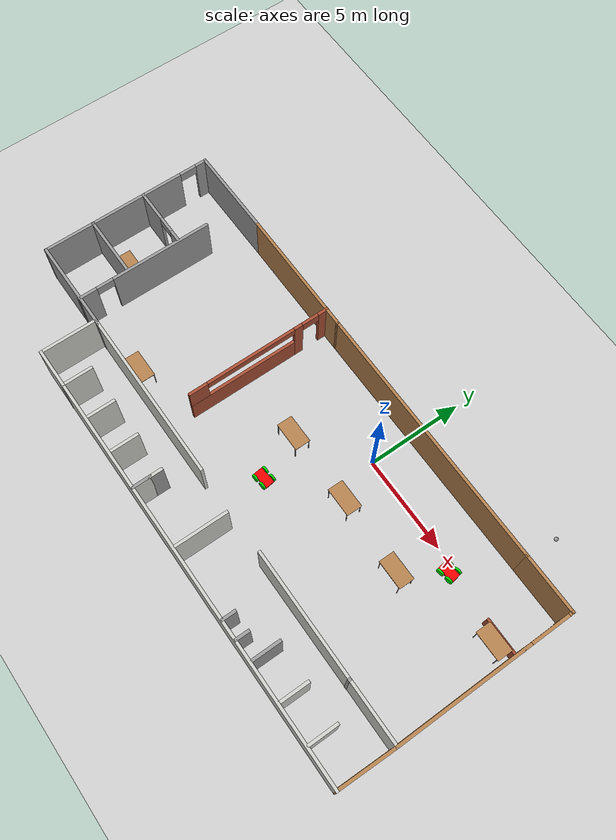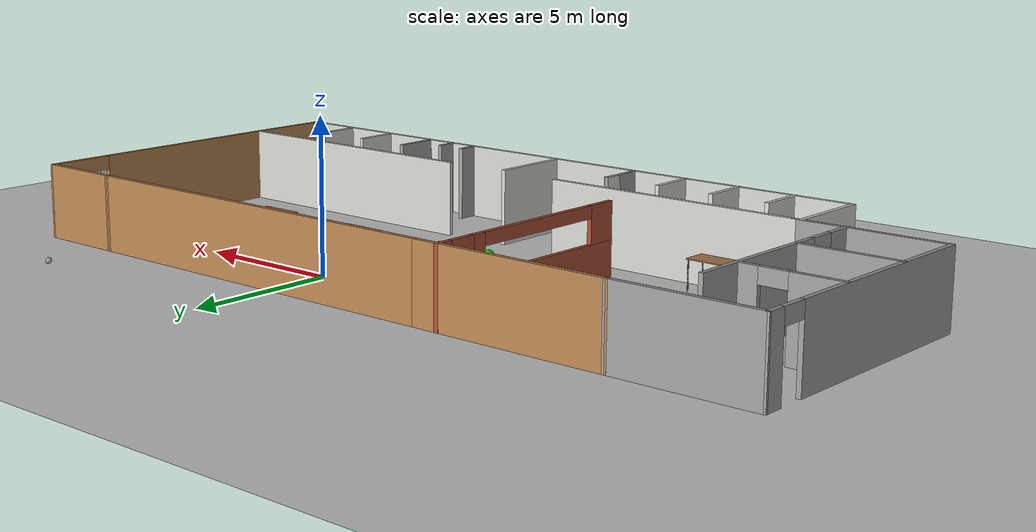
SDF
<sdf version="1.6">
 <world name="default">
  <plugin name="welcome" filename="libwelcome.so"/>
  <light name="sun" type="directional">
   <pose>0 0 10 0 -0 0</pose>
   <diffuse>0.8 0.8 0.8 1</diffuse>
   <specular>0.2 0.2 0.2 1</specular>
   <attenuation>
    <range>1000</range>
    <constant>0.9</constant>
    <linear>0.01</linear>
    <quadratic>0.001</quadratic>
   </attenuation>
   <direction>-0.5 0.1 -0.9</direction>
  </light>
  <model name="ground_plane">
   <static>1</static>
   <link name="link">
    <collision name="collision">
     <geometry><plane><normal>0 0 1</normal><size>100 100</size></plane></geometry>
     <surface><friction><ode><mu>100</mu><mu2>50</mu2></ode></friction></surface>
    </collision>
    <visual name="visual">
     <cast_shadows>0</cast_shadows>
     <geometry><plane><normal>0 0 1</normal><size>100 100</size></plane></geometry>
     <material>
      <script><uri>file://media/materials/scripts/gazebo.material</uri><name>Gazebo/Grey</name></script>
     </material>
    </visual>
   </link>
  </model>
  <gravity>0 0 -9.8</gravity>
  <magnetic_field>6e-06 2.3e-05 -4.2e-05</magnetic_field>
  <atmosphere type="adiabatic"/>
  <physics name="default_physics" default="0" type="ode">
   <max_step_size>0.001</max_step_size>
   <real_time_factor>1</real_time_factor>
   <real_time_update_rate>1000</real_time_update_rate>
  </physics>
  <scene><ambient>0.4 0.4 0.4 1</ambient><background>0.7 0.7 0.7 1</background><shadows>1</shadows></scene>
  <spherical_coordinates>
   <surface_model>EARTH_WGS84</surface_model>
   <latitude_deg>0</latitude_deg>
   <longitude_deg>0</longitude_deg>
   <elevation>0</elevation>
   <heading_deg>0</heading_deg>
  </spherical_coordinates>
  <model name="rest">
   <pose>-3.19031 -3.86827 0 0 -0 0</pose>
   <link name="Wall_105">
    <collision name="Wall_105_Collision">
     <geometry><box><size>1.5 0.15 2.5</size></box></geometry>
     <pose>0 0 1.25 0 -0 0</pose>
    </collision>
    <visual name="Wall_105_Visual">
     <pose>0 0 1.25 0 -0 0</pose>
     <geometry><box><size>1.5 0.15 2.5</size></box></geometry>
     <material>
      <script><uri>file://media/materials/scripts/gazebo.material</uri><name>Gazebo/CeilingTiled</name></script>
      <ambient>1 1 1 1</ambient>
     </material>
     <meta><layer>0</layer></meta>
    </visual>
    <pose>9.84331 -5.22473 0 0 -0 1.5708</pose>
   </link>
   <link name="Wall_107">
    <collision name="Wall_107_Collision">
     <geometry><box><size>1.538 0.15 2.5</size></box></geometry>
     <pose>0 0 1.25 0 -0 0</pose>
    </collision>
    <visual name="Wall_107_Visual">
     <pose>0 0 1.25 0 -0 0</pose>
     <geometry><box><size>1.538 0.15 2.5</size></box></geometry>
     <material>
      <script><uri>file://media/materials/scripts/gazebo.material</uri><name>Gazebo/CeilingTiled</name></script>
      <ambient>1 1 1 1</ambient>
     </material>
     <meta><layer>0</layer></meta>
    </visual>
    <pose>11.8423 -5.24373 0 0 0 -1.5708</pose>
   </link>
   <link name="Wall_109">
    <collision name="Wall_109_Collision">
     <geometry><box><size>0.744777 0.15 2.5</size></box></geometry>
     <pose>0 0 1.25 0 -0 0</pose>
    </collision>
    <visual name="Wall_109_Visual">
     <pose>0 0 1.25 0 -0 0</pose>
     <geometry><box><size>0.744777 0.15 2.5</size></box></geometry>
     <material>
      <script><uri>file://media/materials/scripts/gazebo.material</uri><name>Gazebo/Grey</name></script>
      <ambient>1 1 1 1</ambient>
     </material>
     <meta><layer>0</layer></meta>
    </visual>
    <pose>6.76931 -5.68423 0 0 -0 1.5708</pose>
   </link>
   <link name="Wall_113">
    <collision name="Wall_113_Collision">
     <geometry><box><size>0.745 0.15 2.5</size></box></geometry>
     <pose>0 0 1.25 0 -0 0</pose>
    </collision>
    <visual name="Wall_113_Visual">
     <pose>0 0 1.25 0 -0 0</pose>
     <geometry><box><size>0.745 0.15 2.5</size></box></geometry>
     <material>
      <script><uri>file://media/materials/scripts/gazebo.material</uri><name>Gazebo/Grey</name></script>
      <ambient>1 1 1 1</ambient>
     </material>
     <meta><layer>0</layer></meta>
    </visual>
    <pose>5.76931 -5.68423 0 0 -0 1.5708</pose>
   </link>
   <link name="Wall_115">
    <collision name="Wall_115_Collision">
     <geometry><box><size>1.643 0.15 2.5</size></box></geometry>
     <pose>0 0 1.25 0 -0 0</pose>
    </collision>
    <visual name="Wall_115_Visual">
     <pose>0 0 1.25 0 -0 0</pose>
     <geometry><box><size>1.643 0.15 2.5</size></box></geometry>
     <material>
      <script><uri>file://media/materials/scripts/gazebo.material</uri><name>Gazebo/CeilingTiled</name></script>
      <ambient>1 1 1 1</ambient>
     </material>
     <meta><layer>0</layer></meta>
    </visual>
    <pose>-7.25669 -5.29623 0 0 0 -1.5708</pose>
   </link>
   <link name="Wall_117">
    <collision name="Wall_117_Collision">
     <geometry><box><size>1.59 0.15 2.5</size></box></geometry>
     <pose>0 0 1.25 0 -0 0</pose>
    </collision>
    <visual name="Wall_117_Visual">
     <pose>0 0 1.25 0 -0 0</pose>
     <geometry><box><size>1.59 0.15 2.5</size></box></geometry>
     <material>
      <script><uri>file://media/materials/scripts/gazebo.material</uri><name>Gazebo/CeilingTiled</name></script>
      <ambient>1 1 1 1</ambient>
     </material>
     <meta><layer>0</layer></meta>
    </visual>
    <pose>-5.25669 -5.26973 0 0 0 -1.5708</pose>
   </link>
   <link name="Wall_119">
    <collision name="Wall_119_Collision">
     <geometry><box><size>1.538 0.15 2.5</size></box></geometry>
     <pose>0 0 1.25 0 -0 0</pose>
    </collision>
    <visual name="Wall_119_Visual">
     <pose>0 0 1.25 0 -0 0</pose>
     <geometry><box><size>1.538 0.15 2.5</size></box></geometry>
     <material>
      <script><uri>file://media/materials/scripts/gazebo.material</uri><name>Gazebo/CeilingTiled</name></script>
      <ambient>1 1 1 1</ambient>
     </material>
     <meta><layer>0</layer></meta>
    </visual>
    <pose>-3.25669 -5.24373 0 0 0 -1.5708</pose>
   </link>
   <link name="Wall_121">
    <collision name="Wall_121_Collision">
     <geometry><box><size>1.59 0.15 2.5</size></box></geometry>
     <pose>0 0 1.25 0 -0 0</pose>
    </collision>
    <visual name="Wall_121_Visual">
     <pose>0 0 1.25 0 -0 0</pose>
     <geometry><box><size>1.59 0.15 2.5</size></box></geometry>
     <material>
      <script><uri>file://media/materials/scripts/gazebo.material</uri><name>Gazebo/Grey</name></script>
      <ambient>1 1 1 1</ambient>
     </material>
     <meta><layer>0</layer></meta>
    </visual>
    <pose>-1.25669 -5.26973 0 0 0 -1.5708</pose>
   </link>
   <link name="Wall_122">
    <collision name="Wall_122_Collision">
     <geometry><box><size>1.59 0.15 2.5</size></box></geometry>
     <pose>0 0 1.25 0 -0 0</pose>
    </collision>
    <visual name="Wall_122_Visual">
     <pose>0 0 1.25 0 -0 0</pose>
     <geometry><box><size>1.59 0.15 2.5</size></box></geometry>
     <material>
      <script><uri>file://media/materials/scripts/gazebo.material</uri><name>Gazebo/CeilingTiled</name></script>
      <ambient>1 1 1 1</ambient>
     </material>
     <meta><layer>0</layer></meta>
    </visual>
    <pose>-1.25669 -5.26973 0 0 -0 1.5708</pose>
   </link>
   <link name="Wall_125">
    <collision name="Wall_125_Collision">
     <geometry><box><size>4.79 0.15 2.5</size></box></geometry>
     <pose>0 0 1.25 0 -0 0</pose>
    </collision>
    <visual name="Wall_125_Visual">
     <pose>0 0 1.25 0 -0 0</pose>
     <geometry><box><size>4.79 0.15 2.5</size></box></geometry>
     <material>
      <script><uri>file://media/materials/scripts/gazebo.material</uri><name>Gazebo/Grey</name></script>
      <ambient>1 1 1 1</ambient>
     </material>
     <meta><layer>0</layer></meta>
    </visual>
    <pose>-11.5766 5.9975 0 0 0 -3.13393</pose>
   </link>
   <link name="Wall_126">
    <pose>-13.8966 1.42972 0 0 0 -1.5708</pose>
    <visual name="Wall_126_Visual_0">
     <pose>-4.29481 0 1.25 0 -0 0</pose>
     <geometry><box><size>0.660381 0.15 2.5</size></box></geometry>
     <material>
      <script><uri>file://media/materials/scripts/gazebo.material</uri><name>Gazebo/Grey</name></script>
      <ambient>1 1 1 1</ambient>
     </material>
     <meta><layer>0</layer></meta>
    </visual>
    <collision name="Wall_126_Collision_0">
     <geometry><box><size>0.660381 0.15 2.5</size></box></geometry>
     <pose>-4.29481 0 1.25 0 -0 0</pose>
    </collision>
    <visual name="Wall_126_Visual_1">
     <pose>0.780191 0 1.25 0 -0 0</pose>
     <geometry><box><size>7.68962 0.15 2.5</size></box></geometry>
     <material>
      <script><uri>file://media/materials/scripts/gazebo.material</uri><name>Gazebo/Grey</name></script>
      <ambient>1 1 1 1</ambient>
     </material>
     <meta><layer>0</layer></meta>
    </visual>
    <collision name="Wall_126_Collision_1">
     <geometry><box><size>7.68962 0.15 2.5</size></box></geometry>
     <pose>0.780191 0 1.25 0 -0 0</pose>
    </collision>
    <visual name="Wall_126_Visual_2">
     <pose>-3.51462 0 2.25 0 -0 0</pose>
     <geometry><box><size>0.9 0.15 0.5</size></box></geometry>
     <material>
      <script><uri>file://media/materials/scripts/gazebo.material</uri><name>Gazebo/Grey</name></script>
      <ambient>1 1 1 1</ambient>
     </material>
     <meta><layer>0</layer></meta>
    </visual>
    <collision name="Wall_126_Collision_2">
     <geometry><box><size>0.9 0.15 0.5</size></box></geometry>
     <pose>-3.51462 0 2.25 0 -0 0</pose>
    </collision>
   </link>
   <link name="Wall_128">
    <collision name="Wall_128_Collision">
     <geometry><box><size>5 0.15 2.5</size></box></geometry>
     <pose>0 0 1.25 0 -0 0</pose>
    </collision>
    <visual name="Wall_128_Visual">
     <pose>0 0 1.25 0 -0 0</pose>
     <geometry><box><size>5 0.15 2.5</size></box></geometry>
     <material>
      <script><uri>file://media/materials/scripts/gazebo.material</uri><name>Gazebo/Grey</name></script>
      <ambient>1 1 1 1</ambient>
     </material>
     <meta><layer>0</layer></meta>
    </visual>
    <pose>-11.4532 -3.11873 0 0 -0 3.14159</pose>
   </link>
   <link name="Wall_132">
    <pose>-10.6853 0.397406 0 0 0 -1.5708</pose>
    <visual name="Wall_132_Visual_0">
     <pose>-0.952875 0 1.25 0 -0 0</pose>
     <geometry><box><size>5.34425 0.15 2.5</size></box></geometry>
     <material>
      <script><uri>file://media/materials/scripts/gazebo.material</uri><name>Gazebo/Grey</name></script>
      <ambient>1 1 1 1</ambient>
     </material>
     <meta><layer>0</layer></meta>
    </visual>
    <collision name="Wall_132_Collision_0">
     <geometry><box><size>5.34425 0.15 2.5</size></box></geometry>
     <pose>-0.952875 0 1.25 0 -0 0</pose>
    </collision>
    <visual name="Wall_132_Visual_1">
     <pose>3.12213 0 1.25 0 -0 0</pose>
     <geometry><box><size>1.00575 0.15 2.5</size></box></geometry>
     <material>
      <script><uri>file://media/materials/scripts/gazebo.material</uri><name>Gazebo/Grey</name></script>
      <ambient>1 1 1 1</ambient>
     </material>
     <meta><layer>0</layer></meta>
    </visual>
    <collision name="Wall_132_Collision_1">
     <geometry><box><size>1.00575 0.15 2.5</size></box></geometry>
     <pose>3.12213 0 1.25 0 -0 0</pose>
    </collision>
    <visual name="Wall_132_Visual_2">
     <pose>2.16925 0 2.25 0 -0 0</pose>
     <geometry><box><size>0.9 0.15 0.5</size></box></geometry>
     <material>
      <script><uri>file://media/materials/scripts/gazebo.material</uri><name>Gazebo/Grey</name></script>
      <ambient>1 1 1 1</ambient>
     </material>
     <meta><layer>0</layer></meta>
    </visual>
    <collision name="Wall_132_Collision_2">
     <geometry><box><size>0.9 0.15 0.5</size></box></geometry>
     <pose>2.16925 0 2.25 0 -0 0</pose>
    </collision>
   </link>
   <link name="Wall_134">
    <collision name="Wall_134_Collision">
     <geometry><box><size>3.25 0.15 2.5</size></box></geometry>
     <pose>0 0 1.25 0 -0 0</pose>
    </collision>
    <visual name="Wall_134_Visual">
     <pose>0 0 1.25 0 -0 0</pose>
     <geometry><box><size>3.25 0.15 2.5</size></box></geometry>
     <material>
      <script><uri>file://media/materials/scripts/gazebo.material</uri><name>Gazebo/Grey</name></script>
      <ambient>1 1 1 1</ambient>
     </material>
     <meta><layer>0</layer></meta>
    </visual>
    <pose>-12.3185 -0.49507 0 0 -0 0</pose>
   </link>
   <link name="Wall_137">
    <pose>-12.336 2.3733 0 0 -0 0</pose>
    <visual name="Wall_137_Visual_0">
     <pose>-0.771842 0 1.25 0 -0 0</pose>
     <geometry><box><size>1.70632 0.15 2.5</size></box></geometry>
     <material>
      <script><uri>file://media/materials/scripts/gazebo.material</uri><name>Gazebo/Grey</name></script>
      <ambient>1 1 1 1</ambient>
     </material>
     <meta><layer>0</layer></meta>
    </visual>
    <collision name="Wall_137_Collision_0">
     <geometry><box><size>1.70632 0.15 2.5</size></box></geometry>
     <pose>-0.771842 0 1.25 0 -0 0</pose>
    </collision>
    <visual name="Wall_137_Visual_1">
     <pose>1.30316 0 1.25 0 -0 0</pose>
     <geometry><box><size>0.643683 0.15 2.5</size></box></geometry>
     <material>
      <script><uri>file://media/materials/scripts/gazebo.material</uri><name>Gazebo/Grey</name></script>
      <ambient>1 1 1 1</ambient>
     </material>
     <meta><layer>0</layer></meta>
    </visual>
    <collision name="Wall_137_Collision_1">
     <geometry><box><size>0.643683 0.15 2.5</size></box></geometry>
     <pose>1.30316 0 1.25 0 -0 0</pose>
    </collision>
    <visual name="Wall_137_Visual_2">
     <pose>0.531317 0 2.25 0 -0 0</pose>
     <geometry><box><size>0.9 0.15 0.5</size></box></geometry>
     <material>
      <script><uri>file://media/materials/scripts/gazebo.material</uri><name>Gazebo/Grey</name></script>
      <ambient>1 1 1 1</ambient>
     </material>
     <meta><layer>0</layer></meta>
    </visual>
    <collision name="Wall_137_Collision_2">
     <geometry><box><size>0.9 0.15 0.5</size></box></geometry>
     <pose>0.531317 0 2.25 0 -0 0</pose>
    </collision>
   </link>
   <link name="Wall_3">
    <collision name="Wall_3_Collision">
     <geometry><box><size>13.697 0.15 2.5</size></box></geometry>
     <pose>0 0 1.25 0 -0 0</pose>
    </collision>
    <visual name="Wall_3_Visual">
     <pose>0 0 1.25 0 -0 0</pose>
     <geometry><box><size>13.697 0.15 2.5</size></box></geometry>
     <material>
      <script><uri>file://media/materials/scripts/gazebo.material</uri><name>Gazebo/Wood</name></script>
      <ambient>1 1 1 1</ambient>
     </material>
     <meta><layer>0</layer></meta>
    </visual>
    <pose>4.11681 6.02877 0 0 0 -3.1396</pose>
   </link>
   <link name="Wall_45">
    <collision name="Wall_45_Collision">
     <geometry><box><size>3.1 0.15 2.5</size></box></geometry>
     <pose>0 0 1.25 0 -0 0</pose>
    </collision>
    <visual name="Wall_45_Visual">
     <pose>0 0 1.25 0 -0 0</pose>
     <geometry><box><size>3.1 0.15 2.5</size></box></geometry>
     <material>
      <script><uri>file://media/materials/scripts/gazebo.material</uri><name>Gazebo/Wood</name></script>
      <ambient>1 1 1 1</ambient>
     </material>
     <meta><layer>0</layer></meta>
    </visual>
    <pose>12.3653 6.04227 0 0 -0 0</pose>
   </link>
   <link name="Wall_56">
    <collision name="Wall_56_Collision">
     <geometry><box><size>0.15 0.15 2.5</size></box></geometry>
     <pose>0 0 1.25 0 -0 0</pose>
    </collision>
    <visual name="Wall_56_Visual">
     <pose>0 0 1.25 0 -0 0</pose>
     <geometry><box><size>0.15 0.15 2.5</size></box></geometry>
     <material>
      <script><uri>file://media/materials/scripts/gazebo.material</uri><name>Gazebo/Grey</name></script>
      <ambient>1 1 1 1</ambient>
     </material>
     <meta><layer>0</layer></meta>
    </visual>
    <pose>10.7303 -3.13173 0 0 -0 0</pose>
   </link>
   <link name="Wall_67">
    <collision name="Wall_67_Collision">
     <geometry><box><size>6.75 0.15 2.5</size></box></geometry>
     <pose>0 0 1.25 0 -0 0</pose>
    </collision>
    <visual name="Wall_67_Visual">
     <pose>0 0 1.25 0 -0 0</pose>
     <geometry><box><size>6.75 0.15 2.5</size></box></geometry>
     <material>
      <script><uri>file://media/materials/scripts/gazebo.material</uri><name>Gazebo/Wood</name></script>
      <ambient>1 1 1 1</ambient>
     </material>
     <meta><layer>0</layer></meta>
    </visual>
    <pose>-5.95669 6.01527 0 0 -0 3.14159</pose>
   </link>
   <link name="Wall_73">
    <collision name="Wall_73_Collision">
     <geometry><box><size>0.15 0.15 2.5</size></box></geometry>
     <pose>0 0 1.25 0 -0 0</pose>
    </collision>
    <visual name="Wall_73_Visual">
     <pose>0 0 1.25 0 -0 0</pose>
     <geometry><box><size>0.15 0.15 2.5</size></box></geometry>
     <material>
      <script><uri>file://media/materials/scripts/gazebo.material</uri><name>Gazebo/Grey</name></script>
      <ambient>1 1 1 1</ambient>
     </material>
     <meta><layer>0</layer></meta>
    </visual>
    <pose>13.8608 3.37641 0 0 -0 0</pose>
   </link>
   <link name="Wall_76">
    <pose>13.868 1.46177 0 0 0 -1.56474</pose>
    <visual name="Wall_76_Visual_0">
     <pose>-4.52154 0 1.25 0 -0 0</pose>
     <geometry><box><size>0.268095 0.15 2.5</size></box></geometry>
     <material>
      <script><uri>file://media/materials/scripts/gazebo.material</uri><name>Gazebo/Wood</name></script>
      <ambient>1 1 1 1</ambient>
     </material>
     <meta><layer>0</layer></meta>
    </visual>
    <collision name="Wall_76_Collision_0">
     <geometry><box><size>0.268095 0.15 2.5</size></box></geometry>
     <pose>-4.52154 0 1.25 0 -0 0</pose>
    </collision>
    <visual name="Wall_76_Visual_1">
     <pose>1.14378 0 1.25 0 -0 0</pose>
     <geometry><box><size>7.02361 0.15 2.5</size></box></geometry>
     <material>
      <script><uri>file://media/materials/scripts/gazebo.material</uri><name>Gazebo/Wood</name></script>
      <ambient>1 1 1 1</ambient>
     </material>
     <meta><layer>0</layer></meta>
    </visual>
    <collision name="Wall_76_Collision_1">
     <geometry><box><size>7.02361 0.15 2.5</size></box></geometry>
     <pose>1.14378 0 1.25 0 -0 0</pose>
    </collision>
    <visual name="Wall_76_Visual_2">
     <pose>-3.37776 0 2.25 0 -0 0</pose>
     <geometry><box><size>2.01946 0.15 0.5</size></box></geometry>
     <material>
      <script><uri>file://media/materials/scripts/gazebo.material</uri><name>Gazebo/Wood</name></script>
      <ambient>1 1 1 1</ambient>
     </material>
     <meta><layer>0</layer></meta>
    </visual>
    <collision name="Wall_76_Collision_2">
     <geometry><box><size>2.01946 0.15 0.5</size></box></geometry>
     <pose>-3.37776 0 2.25 0 -0 0</pose>
    </collision>
   </link>
   <link name="Wall_78">
    <pose>-3.55923 2.22695 0 0 0 -1.5708</pose>
    <visual name="Wall_78_Visual_0">
     <pose>-3.58241 0 1.25 0 -0 0</pose>
     <geometry><box><size>0.585178 0.15 2.5</size></box></geometry>
     <material>
      <script><uri>file://media/materials/scripts/gazebo.material</uri><name>Gazebo/Bricks</name></script>
      <ambient>1 1 1 1</ambient>
     </material>
     <meta><layer>0</layer></meta>
    </visual>
    <collision name="Wall_78_Collision_0">
     <geometry><box><size>0.585178 0.15 2.5</size></box></geometry>
     <pose>-3.58241 0 1.25 0 -0 0</pose>
    </collision>
    <visual name="Wall_78_Visual_1">
     <pose>-2.16112 0 1.25 0 -0 0</pose>
     <geometry><box><size>0.457397 0.15 2.5</size></box></geometry>
     <material>
      <script><uri>file://media/materials/scripts/gazebo.material</uri><name>Gazebo/Bricks</name></script>
      <ambient>1 1 1 1</ambient>
     </material>
     <meta><layer>0</layer></meta>
    </visual>
    <collision name="Wall_78_Collision_1">
     <geometry><box><size>0.457397 0.15 2.5</size></box></geometry>
     <pose>-2.16112 0 1.25 0 -0 0</pose>
    </collision>
    <visual name="Wall_78_Visual_2">
     <pose>0.971288 0 0.65 0 -0 0</pose>
     <geometry><box><size>5.80743 0.15 1.3</size></box></geometry>
     <material>
      <script><uri>file://media/materials/scripts/gazebo.material</uri><name>Gazebo/Bricks</name></script>
      <ambient>1 1 1 1</ambient>
     </material>
     <meta><layer>0</layer></meta>
    </visual>
    <collision name="Wall_78_Collision_2">
     <geometry><box><size>5.80743 0.15 1.3</size></box></geometry>
     <pose>0.971288 0 0.65 0 -0 0</pose>
    </collision>
    <visual name="Wall_78_Visual_3">
     <pose>3.37129 0 1.9 0 -0 0</pose>
     <geometry><box><size>1.00743 0.15 1.2</size></box></geometry>
     <material>
      <script><uri>file://media/materials/scripts/gazebo.material</uri><name>Gazebo/Bricks</name></script>
      <ambient>1 1 1 1</ambient>
     </material>
     <meta><layer>0</layer></meta>
    </visual>
    <collision name="Wall_78_Collision_3">
     <geometry><box><size>1.00743 0.15 1.2</size></box></geometry>
     <pose>3.37129 0 1.9 0 -0 0</pose>
    </collision>
    <visual name="Wall_78_Visual_4">
     <pose>-2.83982 0 2.25 0 -0 0</pose>
     <geometry><box><size>0.9 0.15 0.5</size></box></geometry>
     <material>
      <script><uri>file://media/materials/scripts/gazebo.material</uri><name>Gazebo/Bricks</name></script>
      <ambient>1 1 1 1</ambient>
     </material>
     <meta><layer>0</layer></meta>
    </visual>
    <collision name="Wall_78_Collision_4">
     <geometry><box><size>0.9 0.15 0.5</size></box></geometry>
     <pose>-2.83982 0 2.25 0 -0 0</pose>
    </collision>
    <visual name="Wall_78_Visual_5">
     <pose>0.467575 0 2.3 0 -0 0</pose>
     <geometry><box><size>4.8 0.15 0.4</size></box></geometry>
     <material>
      <script><uri>file://media/materials/scripts/gazebo.material</uri><name>Gazebo/Bricks</name></script>
      <ambient>1 1 1 1</ambient>
     </material>
     <meta><layer>0</layer></meta>
    </visual>
    <collision name="Wall_78_Collision_5">
     <geometry><box><size>4.8 0.15 0.4</size></box></geometry>
     <pose>0.467575 0 2.3 0 -0 0</pose>
    </collision>
   </link>
   <link name="Wall_80">
    <collision name="Wall_80_Collision">
     <geometry><box><size>1.99 0.14 1</size></box></geometry>
     <pose>0 0 0.5 0 -0 0</pose>
    </collision>
    <visual name="Wall_80_Visual">
     <pose>0 0 0.5 0 -0 0</pose>
     <geometry><box><size>1.99 0.14 1</size></box></geometry>
     <material>
      <script><uri>file://media/materials/scripts/gazebo.material</uri><name>Gazebo/Bricks</name></script>
      <ambient>1 1 1 1</ambient>
     </material>
     <meta><layer>0</layer></meta>
    </visual>
    <pose>12.9358 3.3939 0 0 -0 3.14159</pose>
   </link>
   <link name="Wall_84">
    <collision name="Wall_84_Collision">
     <geometry><box><size>3.04349 0.15 2.5</size></box></geometry>
     <pose>0 0 1.25 0 -0 0</pose>
    </collision>
    <visual name="Wall_84_Visual">
     <pose>0 0 1.25 0 -0 0</pose>
     <geometry><box><size>3.04349 0.15 2.5</size></box></geometry>
     <material>
      <script><uri>file://media/materials/scripts/gazebo.material</uri><name>Gazebo/CeilingTiled</name></script>
      <ambient>1 1 1 1</ambient>
     </material>
     <meta><layer>0</layer></meta>
    </visual>
    <pose>-9.25669 -4.57798 0 0 0 -1.5708</pose>
   </link>
   <link name="Wall_85">
    <collision name="Wall_85_Collision">
     <geometry><box><size>23.25 0.15 2.5</size></box></geometry>
     <pose>0 0 1.25 0 -0 0</pose>
    </collision>
    <visual name="Wall_85_Visual">
     <pose>0 0 1.25 0 -0 0</pose>
     <geometry><box><size>23.25 0.15 2.5</size></box></geometry>
     <material>
      <script><uri>file://media/materials/scripts/gazebo.material</uri><name>Gazebo/CeilingTiled</name></script>
      <ambient>1 1 1 1</ambient>
     </material>
     <meta><layer>0</layer></meta>
    </visual>
    <pose>2.29331 -6.02473 0 0 -0 0</pose>
   </link>
   <link name="Wall_86">
    <collision name="Wall_86_Collision">
     <geometry><box><size>3.05647 0.15 2.5</size></box></geometry>
     <pose>0 0 1.25 0 -0 0</pose>
    </collision>
    <visual name="Wall_86_Visual">
     <pose>0 0 1.25 0 -0 0</pose>
     <geometry><box><size>3.05647 0.15 2.5</size></box></geometry>
     <material>
      <script><uri>file://media/materials/scripts/gazebo.material</uri><name>Gazebo/Wood</name></script>
      <ambient>1 1 1 1</ambient>
     </material>
     <meta><layer>0</layer></meta>
    </visual>
    <pose>13.8695 -4.57173 0 0 -0 1.55274</pose>
   </link>
   <link name="Wall_93">
    <collision name="Wall_93_Collision">
     <geometry><box><size>8.93004 0.15 2.5</size></box></geometry>
     <pose>0 0 1.25 0 -0 0</pose>
    </collision>
    <visual name="Wall_93_Visual">
     <pose>0 0 1.25 0 -0 0</pose>
     <geometry><box><size>8.93004 0.15 2.5</size></box></geometry>
     <material>
      <script><uri>file://media/materials/scripts/gazebo.material</uri><name>Gazebo/CeilingTiled</name></script>
      <ambient>1 1 1 1</ambient>
     </material>
     <meta><layer>0</layer></meta>
    </visual>
    <pose>-4.65571 -3.11873 0 0 -0 3.14159</pose>
   </link>
   <link name="Wall_95">
    <collision name="Wall_95_Collision">
     <geometry><box><size>9.75 0.15 2.5</size></box></geometry>
     <pose>0 0 1.25 0 -0 0</pose>
    </collision>
    <visual name="Wall_95_Visual">
     <pose>0 0 1.25 0 -0 0</pose>
     <geometry><box><size>9.75 0.15 2.5</size></box></geometry>
     <material>
      <script><uri>file://media/materials/scripts/gazebo.material</uri><name>Gazebo/CeilingTiled</name></script>
      <ambient>1 1 1 1</ambient>
     </material>
     <meta><layer>0</layer></meta>
    </visual>
    <pose>9.09578 -3.11873 0 0 -0 0</pose>
   </link>
   <link name="Wall_97">
    <collision name="Wall_97_Collision">
     <geometry><box><size>2.75 0.15 2.5</size></box></geometry>
     <pose>0 0 1.25 0 -0 0</pose>
    </collision>
    <visual name="Wall_97_Visual">
     <pose>0 0 1.25 0 -0 0</pose>
     <geometry><box><size>2.75 0.15 2.5</size></box></geometry>
     <material>
      <script><uri>file://media/materials/scripts/gazebo.material</uri><name>Gazebo/CeilingTiled</name></script>
      <ambient>1 1 1 1</ambient>
     </material>
     <meta><layer>0</layer></meta>
    </visual>
    <pose>2.01248 -4.59348 0 0 0 -1.5708</pose>
   </link>
   <link name="Wall_99">
    <collision name="Wall_99_Collision">
     <geometry><box><size>1.5 0.15 2.5</size></box></geometry>
     <pose>0 0 1.25 0 -0 0</pose>
    </collision>
    <visual name="Wall_99_Visual">
     <pose>0 0 1.25 0 -0 0</pose>
     <geometry><box><size>1.5 0.15 2.5</size></box></geometry>
     <material>
      <script><uri>file://media/materials/scripts/gazebo.material</uri><name>Gazebo/Grey</name></script>
      <ambient>1 1 1 1</ambient>
     </material>
     <meta><layer>0</layer></meta>
    </visual>
    <pose>7.84331 -5.22473 0 0 -0 1.5708</pose>
   </link>
   <static>1</static>
  </model>
  <model name="table">
   <static>1</static>
   <link name="link">
    <collision name="surface">
     <pose>0 0 1 0 -0 0</pose>
     <geometry><box><size>1.5 0.8 0.03</size></box></geometry>
     <surface><friction><ode><mu>0.6</mu><mu2>0.6</mu2></ode></friction></surface>
    </collision>
    <visual name="visual1">
     <pose>0 0 1 0 -0 0</pose>
     <geometry><box><size>1.5 0.8 0.03</size></box></geometry>
     <material>
      <script><uri>file://media/materials/scripts/gazebo.material</uri><name>Gazebo/Wood</name></script>
     </material>
    </visual>
    <collision name="front_left_leg">
     <pose>0.68 0.38 0.5 0 -0 0</pose>
     <geometry><cylinder><radius>0.02</radius><length>1</length></cylinder></geometry>
    </collision>
    <visual name="front_left_leg">
     <pose>0.68 0.38 0.5 0 -0 0</pose>
     <geometry><cylinder><radius>0.02</radius><length>1</length></cylinder></geometry>
     <material>
      <script><uri>file://media/materials/scripts/gazebo.material</uri><name>Gazebo/Grey</name></script>
     </material>
    </visual>
    <collision name="front_right_leg">
     <pose>0.68 -0.38 0.5 0 -0 0</pose>
     <geometry><cylinder><radius>0.02</radius><length>1</length></cylinder></geometry>
    </collision>
    <visual name="front_right_leg">
     <pose>0.68 -0.38 0.5 0 -0 0</pose>
     <geometry><cylinder><radius>0.02</radius><length>1</length></cylinder></geometry>
     <material>
      <script><uri>file://media/materials/scripts/gazebo.material</uri><name>Gazebo/Grey</name></script>
     </material>
    </visual>
    <collision name="back_right_leg">
     <pose>-0.68 -0.38 0.5 0 -0 0</pose>
     <geometry><cylinder><radius>0.02</radius><length>1</length></cylinder></geometry>
    </collision>
    <visual name="back_right_leg">
     <pose>-0.68 -0.38 0.5 0 -0 0</pose>
     <geometry><cylinder><radius>0.02</radius><length>1</length></cylinder></geometry>
     <material>
      <script><uri>file://media/materials/scripts/gazebo.material</uri><name>Gazebo/Grey</name></script>
     </material>
    </visual>
    <collision name="back_left_leg">
     <pose>-0.68 0.38 0.5 0 -0 0</pose>
     <geometry><cylinder><radius>0.02</radius><length>1</length></cylinder></geometry>
    </collision>
    <visual name="back_left_leg">
     <pose>-0.68 0.38 0.5 0 -0 0</pose>
     <geometry><cylinder><radius>0.02</radius><length>1</length></cylinder></geometry>
     <material>
      <script><uri>file://media/materials/scripts/gazebo.material</uri><name>Gazebo/Grey</name></script>
     </material>
    </visual>
   </link>
   <pose>9.67368 -0.862444 0 0 -0 0</pose>
  </model>
  <model name="table_0">
   <static>1</static>
   <link name="link">
    <collision name="surface">
     <pose>0 0 1 0 -0 0</pose>
     <geometry><box><size>1.5 0.8 0.03</size></box></geometry>
     <surface><friction><ode><mu>0.6</mu><mu2>0.6</mu2></ode></friction></surface>
    </collision>
    <visual name="visual1">
     <pose>0 0 1 0 -0 0</pose>
     <geometry><box><size>1.5 0.8 0.03</size></box></geometry>
     <material>
      <script><uri>file://media/materials/scripts/gazebo.material</uri><name>Gazebo/Wood</name></script>
     </material>
    </visual>
    <collision name="front_left_leg">
     <pose>0.68 0.38 0.5 0 -0 0</pose>
     <geometry><cylinder><radius>0.02</radius><length>1</length></cylinder></geometry>
    </collision>
    <visual name="front_left_leg">
     <pose>0.68 0.38 0.5 0 -0 0</pose>
     <geometry><cylinder><radius>0.02</radius><length>1</length></cylinder></geometry>
     <material>
      <script><uri>file://media/materials/scripts/gazebo.material</uri><name>Gazebo/Grey</name></script>
     </material>
    </visual>
    <collision name="front_right_leg">
     <pose>0.68 -0.38 0.5 0 -0 0</pose>
     <geometry><cylinder><radius>0.02</radius><length>1</length></cylinder></geometry>
    </collision>
    <visual name="front_right_leg">
     <pose>0.68 -0.38 0.5 0 -0 0</pose>
     <geometry><cylinder><radius>0.02</radius><length>1</length></cylinder></geometry>
     <material>
      <script><uri>file://media/materials/scripts/gazebo.material</uri><name>Gazebo/Grey</name></script>
     </material>
    </visual>
    <collision name="back_right_leg">
     <pose>-0.68 -0.38 0.5 0 -0 0</pose>
     <geometry><cylinder><radius>0.02</radius><length>1</length></cylinder></geometry>
    </collision>
    <visual name="back_right_leg">
     <pose>-0.68 -0.38 0.5 0 -0 0</pose>
     <geometry><cylinder><radius>0.02</radius><length>1</length></cylinder></geometry>
     <material>
      <script><uri>file://media/materials/scripts/gazebo.material</uri><name>Gazebo/Grey</name></script>
     </material>
    </visual>
    <collision name="back_left_leg">
     <pose>-0.68 0.38 0.5 0 -0 0</pose>
     <geometry><cylinder><radius>0.02</radius><length>1</length></cylinder></geometry>
    </collision>
    <visual name="back_left_leg">
     <pose>-0.68 0.38 0.5 0 -0 0</pose>
     <geometry><cylinder><radius>0.02</radius><length>1</length></cylinder></geometry>
     <material>
      <script><uri>file://media/materials/scripts/gazebo.material</uri><name>Gazebo/Grey</name></script>
     </material>
    </visual>
   </link>
   <pose>-3.01466 -2.3576 0 0 -0 0</pose>
  </model>
  <model name="table_1">
   <static>1</static>
   <link name="link">
    <collision name="surface">
     <pose>0 0 1 0 -0 0</pose>
     <geometry><box><size>1.5 0.8 0.03</size></box></geometry>
     <surface><friction><ode><mu>0.6</mu><mu2>0.6</mu2></ode></friction></surface>
    </collision>
    <visual name="visual1">
     <pose>0 0 1 0 -0 0</pose>
     <geometry><box><size>1.5 0.8 0.03</size></box></geometry>
     <material>
      <script><uri>file://media/materials/scripts/gazebo.material</uri><name>Gazebo/Wood</name></script>
     </material>
    </visual>
    <collision name="front_left_leg">
     <pose>0.68 0.38 0.5 0 -0 0</pose>
     <geometry><cylinder><radius>0.02</radius><length>1</length></cylinder></geometry>
    </collision>
    <visual name="front_left_leg">
     <pose>0.68 0.38 0.5 0 -0 0</pose>
     <geometry><cylinder><radius>0.02</radius><length>1</length></cylinder></geometry>
     <material>
      <script><uri>file://media/materials/scripts/gazebo.material</uri><name>Gazebo/Grey</name></script>
     </material>
    </visual>
    <collision name="front_right_leg">
     <pose>0.68 -0.38 0.5 0 -0 0</pose>
     <geometry><cylinder><radius>0.02</radius><length>1</length></cylinder></geometry>
    </collision>
    <visual name="front_right_leg">
     <pose>0.68 -0.38 0.5 0 -0 0</pose>
     <geometry><cylinder><radius>0.02</radius><length>1</length></cylinder></geometry>
     <material>
      <script><uri>file://media/materials/scripts/gazebo.material</uri><name>Gazebo/Grey</name></script>
     </material>
    </visual>
    <collision name="back_right_leg">
     <pose>-0.68 -0.38 0.5 0 -0 0</pose>
     <geometry><cylinder><radius>0.02</radius><length>1</length></cylinder></geometry>
    </collision>
    <visual name="back_right_leg">
     <pose>-0.68 -0.38 0.5 0 -0 0</pose>
     <geometry><cylinder><radius>0.02</radius><length>1</length></cylinder></geometry>
     <material>
      <script><uri>file://media/materials/scripts/gazebo.material</uri><name>Gazebo/Grey</name></script>
     </material>
    </visual>
    <collision name="back_left_leg">
     <pose>-0.68 0.38 0.5 0 -0 0</pose>
     <geometry><cylinder><radius>0.02</radius><length>1</length></cylinder></geometry>
    </collision>
    <visual name="back_left_leg">
     <pose>-0.68 0.38 0.5 0 -0 0</pose>
     <geometry><cylinder><radius>0.02</radius><length>1</length></cylinder></geometry>
     <material>
      <script><uri>file://media/materials/scripts/gazebo.material</uri><name>Gazebo/Grey</name></script>
     </material>
    </visual>
   </link>
   <pose>0.877917 -2.27792 0 0 -0 0</pose>
  </model>
  <model name="table_2">
   <static>1</static>
   <link name="link">
    <collision name="surface">
     <pose>0 0 1 0 -0 0</pose>
     <geometry><box><size>1.5 0.8 0.03</size></box></geometry>
     <surface><friction><ode><mu>0.6</mu><mu2>0.6</mu2></ode></friction></surface>
    </collision>
    <visual name="visual1">
     <pose>0 0 1 0 -0 0</pose>
     <geometry><box><size>1.5 0.8 0.03</size></box></geometry>
     <material>
      <script><uri>file://media/materials/scripts/gazebo.material</uri><name>Gazebo/Wood</name></script>
     </material>
    </visual>
    <collision name="front_left_leg">
     <pose>0.68 0.38 0.5 0 -0 0</pose>
     <geometry><cylinder><radius>0.02</radius><length>1</length></cylinder></geometry>
    </collision>
    <visual name="front_left_leg">
     <pose>0.68 0.38 0.5 0 -0 0</pose>
     <geometry><cylinder><radius>0.02</radius><length>1</length></cylinder></geometry>
     <material>
      <script><uri>file://media/materials/scripts/gazebo.material</uri><name>Gazebo/Grey</name></script>
     </material>
    </visual>
    <collision name="front_right_leg">
     <pose>0.68 -0.38 0.5 0 -0 0</pose>
     <geometry><cylinder><radius>0.02</radius><length>1</length></cylinder></geometry>
    </collision>
    <visual name="front_right_leg">
     <pose>0.68 -0.38 0.5 0 -0 0</pose>
     <geometry><cylinder><radius>0.02</radius><length>1</length></cylinder></geometry>
     <material>
      <script><uri>file://media/materials/scripts/gazebo.material</uri><name>Gazebo/Grey</name></script>
     </material>
    </visual>
    <collision name="back_right_leg">
     <pose>-0.68 -0.38 0.5 0 -0 0</pose>
     <geometry><cylinder><radius>0.02</radius><length>1</length></cylinder></geometry>
    </collision>
    <visual name="back_right_leg">
     <pose>-0.68 -0.38 0.5 0 -0 0</pose>
     <geometry><cylinder><radius>0.02</radius><length>1</length></cylinder></geometry>
     <material>
      <script><uri>file://media/materials/scripts/gazebo.material</uri><name>Gazebo/Grey</name></script>
     </material>
    </visual>
    <collision name="back_left_leg">
     <pose>-0.68 0.38 0.5 0 -0 0</pose>
     <geometry><cylinder><radius>0.02</radius><length>1</length></cylinder></geometry>
    </collision>
    <visual name="back_left_leg">
     <pose>-0.68 0.38 0.5 0 -0 0</pose>
     <geometry><cylinder><radius>0.02</radius><length>1</length></cylinder></geometry>
     <material>
      <script><uri>file://media/materials/scripts/gazebo.material</uri><name>Gazebo/Grey</name></script>
     </material>
    </visual>
   </link>
   <pose>4.8441 -2.38743 0 0 -0 0</pose>
  </model>
  <model name="table_3">
   <static>1</static>
   <link name="link">
    <collision name="surface">
     <pose>0 0 1 0 -0 0</pose>
     <geometry><box><size>1.5 0.8 0.03</size></box></geometry>
     <surface><friction><ode><mu>0.6</mu><mu2>0.6</mu2></ode></friction></surface>
    </collision>
    <visual name="visual1">
     <pose>0 0 1 0 -0 0</pose>
     <geometry><box><size>1.5 0.8 0.03</size></box></geometry>
     <material>
      <script><uri>file://media/materials/scripts/gazebo.material</uri><name>Gazebo/Wood</name></script>
     </material>
    </visual>
    <collision name="front_left_leg">
     <pose>0.68 0.38 0.5 0 -0 0</pose>
     <geometry><cylinder><radius>0.02</radius><length>1</length></cylinder></geometry>
    </collision>
    <visual name="front_left_leg">
     <pose>0.68 0.38 0.5 0 -0 0</pose>
     <geometry><cylinder><radius>0.02</radius><length>1</length></cylinder></geometry>
     <material>
      <script><uri>file://media/materials/scripts/gazebo.material</uri><name>Gazebo/Grey</name></script>
     </material>
    </visual>
    <collision name="front_right_leg">
     <pose>0.68 -0.38 0.5 0 -0 0</pose>
     <geometry><cylinder><radius>0.02</radius><length>1</length></cylinder></geometry>
    </collision>
    <visual name="front_right_leg">
     <pose>0.68 -0.38 0.5 0 -0 0</pose>
     <geometry><cylinder><radius>0.02</radius><length>1</length></cylinder></geometry>
     <material>
      <script><uri>file://media/materials/scripts/gazebo.material</uri><name>Gazebo/Grey</name></script>
     </material>
    </visual>
    <collision name="back_right_leg">
     <pose>-0.68 -0.38 0.5 0 -0 0</pose>
     <geometry><cylinder><radius>0.02</radius><length>1</length></cylinder></geometry>
    </collision>
    <visual name="back_right_leg">
     <pose>-0.68 -0.38 0.5 0 -0 0</pose>
     <geometry><cylinder><radius>0.02</radius><length>1</length></cylinder></geometry>
     <material>
      <script><uri>file://media/materials/scripts/gazebo.material</uri><name>Gazebo/Grey</name></script>
     </material>
    </visual>
    <collision name="back_left_leg">
     <pose>-0.68 0.38 0.5 0 -0 0</pose>
     <geometry><cylinder><radius>0.02</radius><length>1</length></cylinder></geometry>
    </collision>
    <visual name="back_left_leg">
     <pose>-0.68 0.38 0.5 0 -0 0</pose>
     <geometry><cylinder><radius>0.02</radius><length>1</length></cylinder></geometry>
     <material>
      <script><uri>file://media/materials/scripts/gazebo.material</uri><name>Gazebo/Grey</name></script>
     </material>
    </visual>
   </link>
   <pose>-9.95885 -6.40768 0 0 -0 0</pose>
  </model>
  <model name="table_4">
   <static>1</static>
   <link name="link">
    <collision name="surface">
     <pose>0 0 1 0 -0 0</pose>
     <geometry><box><size>1.5 0.8 0.03</size></box></geometry>
     <surface><friction><ode><mu>0.6</mu><mu2>0.6</mu2></ode></friction></surface>
    </collision>
    <visual name="visual1">
     <pose>0 0 1 0 -0 0</pose>
     <geometry><box><size>1.5 0.8 0.03</size></box></geometry>
     <material>
      <script><uri>file://media/materials/scripts/gazebo.material</uri><name>Gazebo/Wood</name></script>
     </material>
    </visual>
    <collision name="front_left_leg">
     <pose>0.68 0.38 0.5 0 -0 0</pose>
     <geometry><cylinder><radius>0.02</radius><length>1</length></cylinder></geometry>
    </collision>
    <visual name="front_left_leg">
     <pose>0.68 0.38 0.5 0 -0 0</pose>
     <geometry><cylinder><radius>0.02</radius><length>1</length></cylinder></geometry>
     <material>
      <script><uri>file://media/materials/scripts/gazebo.material</uri><name>Gazebo/Grey</name></script>
     </material>
    </visual>
    <collision name="front_right_leg">
     <pose>0.68 -0.38 0.5 0 -0 0</pose>
     <geometry><cylinder><radius>0.02</radius><length>1</length></cylinder></geometry>
    </collision>
    <visual name="front_right_leg">
     <pose>0.68 -0.38 0.5 0 -0 0</pose>
     <geometry><cylinder><radius>0.02</radius><length>1</length></cylinder></geometry>
     <material>
      <script><uri>file://media/materials/scripts/gazebo.material</uri><name>Gazebo/Grey</name></script>
     </material>
    </visual>
    <collision name="back_right_leg">
     <pose>-0.68 -0.38 0.5 0 -0 0</pose>
     <geometry><cylinder><radius>0.02</radius><length>1</length></cylinder></geometry>
    </collision>
    <visual name="back_right_leg">
     <pose>-0.68 -0.38 0.5 0 -0 0</pose>
     <geometry><cylinder><radius>0.02</radius><length>1</length></cylinder></geometry>
     <material>
      <script><uri>file://media/materials/scripts/gazebo.material</uri><name>Gazebo/Grey</name></script>
     </material>
    </visual>
    <collision name="back_left_leg">
     <pose>-0.68 0.38 0.5 0 -0 0</pose>
     <geometry><cylinder><radius>0.02</radius><length>1</length></cylinder></geometry>
    </collision>
    <visual name="back_left_leg">
     <pose>-0.68 0.38 0.5 0 -0 0</pose>
     <geometry><cylinder><radius>0.02</radius><length>1</length></cylinder></geometry>
     <material>
      <script><uri>file://media/materials/scripts/gazebo.material</uri><name>Gazebo/Grey</name></script>
     </material>
    </visual>
   </link>
   <pose>-14.9673 -3.812 0 0 -0 0</pose>
  </model>
  <model name="newrobo">
   <link name="link_0">
    <pose>-0.020707 0.020259 0.5 0 -0 0</pose>
    <inertial>
     <mass>1</mass>
     <inertia>
      <ixx>0.166667</ixx>
      <ixy>0</ixy>
      <ixz>0</ixz>
      <iyy>0.166667</iyy>
      <iyz>0</iyz>
      <izz>0.166667</izz>
     </inertia>
     <pose>0 0 0.2 0 -0 0</pose>
    </inertial>
    <visual name="visual">
     <geometry><box><size>0.9 0.5 0.1</size></box></geometry>
     <material>
      <lighting>1</lighting>
      <script><uri>file://media/materials/scripts/gazebo.material</uri><name>Gazebo/Grey</name></script>
      <shader type="pixel"><normal_map>__default__</normal_map></shader>
      <ambient>1 0 0 1</ambient>
      <diffuse>1 0 0 1</diffuse>
      <specular>1 0 1 1</specular>
      <emissive>1 0 0 1</emissive>
     </material>
    </visual>
    <collision name="collision">
     <geometry><box><size>0.9 0.5 0.1</size></box></geometry>
     <surface>
      <friction>
       <ode><mu>1</mu><mu2>1</mu2><fdir1>0 0 0</fdir1><slip1>0</slip1><slip2>0</slip2></ode>
       <torsional>
        <coefficient>1</coefficient>
        <patch_radius>0</patch_radius>
        <surface_radius>0</surface_radius>
        <use_patch_radius>1</use_patch_radius>
        <ode><slip>0</slip></ode>
       </torsional>
      </friction>
      <bounce><restitution_coefficient>0</restitution_coefficient><threshold>1e+06</threshold></bounce>
      <contact>
       <collide_without_contact>0</collide_without_contact>
       <collide_without_contact_bitmask>1</collide_without_contact_bitmask>
       <collide_bitmask>1</collide_bitmask>
       <ode>
        <soft_cfm>0</soft_cfm>
        <soft_erp>0.2</soft_erp>
        <kp>1e+13</kp>
        <kd>1</kd>
        <max_vel>0.01</max_vel>
        <min_depth>0</min_depth>
       </ode>
       <bullet>
        <split_impulse>1</split_impulse>
        <split_impulse_penetration_threshold>-0.01</split_impulse_penetration_threshold>
        <soft_cfm>0</soft_cfm>
        <soft_erp>0.2</soft_erp>
        <kp>1e+13</kp>
        <kd>1</kd>
       </bullet>
      </contact>
     </surface>
    </collision>
   </link>
   <link name="link_1">
    <pose>0.229293 -0.27976 0.544996 1.5707 -0 0</pose>
    <inertial>
     <mass>1</mass>
     <inertia><ixx>0.145833</ixx><ixy>0</ixy><ixz>0</ixz><iyy>0.145833</iyy><iyz>0</iyz><izz>0.125</izz></inertia>
    </inertial>
    <visual name="visual">
     <geometry><cylinder><radius>0.2</radius><length>0.1</length></cylinder></geometry>
     <material>
      <lighting>1</lighting>
      <script><uri>file://media/materials/scripts/gazebo.material</uri><name>Gazebo/Grey</name></script>
      <shader type="pixel"><normal_map>__default__</normal_map></shader>
      <ambient>0 1 0 1</ambient>
      <diffuse>0 1 0 1</diffuse>
      <specular>0 1 0 1</specular>
      <emissive>0 1 0 1</emissive>
     </material>
    </visual>
    <collision name="collision">
     <geometry><cylinder><radius>0.2</radius><length>0.1</length></cylinder></geometry>
     <surface>
      <friction>
       <ode><mu>1</mu><mu2>1</mu2><fdir1>0 0 0</fdir1><slip1>0</slip1><slip2>0</slip2></ode>
       <torsional>
        <coefficient>1</coefficient>
        <patch_radius>0</patch_radius>
        <surface_radius>0</surface_radius>
        <use_patch_radius>1</use_patch_radius>
        <ode><slip>0</slip></ode>
       </torsional>
      </friction>
      <bounce><restitution_coefficient>0</restitution_coefficient><threshold>1e+06</threshold></bounce>
      <contact>
       <collide_without_contact>0</collide_without_contact>
       <collide_without_contact_bitmask>1</collide_without_contact_bitmask>
       <collide_bitmask>1</collide_bitmask>
       <ode>
        <soft_cfm>0</soft_cfm>
        <soft_erp>0.2</soft_erp>
        <kp>1e+13</kp>
        <kd>1</kd>
        <max_vel>0.01</max_vel>
        <min_depth>0</min_depth>
       </ode>
       <bullet>
        <split_impulse>1</split_impulse>
        <split_impulse_penetration_threshold>-0.01</split_impulse_penetration_threshold>
        <soft_cfm>0</soft_cfm>
        <soft_erp>0.2</soft_erp>
        <kp>1e+13</kp>
        <kd>1</kd>
       </bullet>
      </contact>
     </surface>
    </collision>
   </link>
   <link name="link_1_clone">
    <pose>0.229293 0.320278 0.545 1.5707 -0 0</pose>
    <inertial>
     <mass>1</mass>
     <inertia><ixx>0.145833</ixx><ixy>0</ixy><ixz>0</ixz><iyy>0.145833</iyy><iyz>0</iyz><izz>0.125</izz></inertia>
    </inertial>
    <visual name="visual">
     <geometry><cylinder><radius>0.2</radius><length>0.1</length></cylinder></geometry>
     <material>
      <lighting>1</lighting>
      <script><uri>file://media/materials/scripts/gazebo.material</uri><name>Gazebo/Grey</name></script>
      <shader type="pixel"><normal_map>__default__</normal_map></shader>
      <ambient>0 1 0 1</ambient>
      <diffuse>0 1 0 1</diffuse>
      <specular>0 1 0 1</specular>
      <emissive>0 1 0 1</emissive>
     </material>
    </visual>
    <collision name="collision">
     <geometry><cylinder><radius>0.2</radius><length>0.1</length></cylinder></geometry>
     <surface>
      <friction>
       <ode><mu>1</mu><mu2>1</mu2><fdir1>0 0 0</fdir1><slip1>0</slip1><slip2>0</slip2></ode>
       <torsional>
        <coefficient>1</coefficient>
        <patch_radius>0</patch_radius>
        <surface_radius>0</surface_radius>
        <use_patch_radius>1</use_patch_radius>
        <ode><slip>0</slip></ode>
       </torsional>
      </friction>
      <bounce><restitution_coefficient>0</restitution_coefficient><threshold>1e+06</threshold></bounce>
      <contact>
       <collide_without_contact>0</collide_without_contact>
       <collide_without_contact_bitmask>1</collide_without_contact_bitmask>
       <collide_bitmask>1</collide_bitmask>
       <ode>
        <soft_cfm>0</soft_cfm>
        <soft_erp>0.2</soft_erp>
        <kp>1e+13</kp>
        <kd>1</kd>
        <max_vel>0.01</max_vel>
        <min_depth>0</min_depth>
       </ode>
       <bullet>
        <split_impulse>1</split_impulse>
        <split_impulse_penetration_threshold>-0.01</split_impulse_penetration_threshold>
        <soft_cfm>0</soft_cfm>
        <soft_erp>0.2</soft_erp>
        <kp>1e+13</kp>
        <kd>1</kd>
       </bullet>
      </contact>
     </surface>
    </collision>
   </link>
   <link name="link_1_clone_0">
    <pose>-0.270707 0.320278 0.545 1.5707 -0 0</pose>
    <inertial>
     <mass>1</mass>
     <inertia><ixx>0.145833</ixx><ixy>0</ixy><ixz>0</ixz><iyy>0.145833</iyy><iyz>0</iyz><izz>0.125</izz></inertia>
    </inertial>
    <visual name="visual">
     <geometry><cylinder><radius>0.2</radius><length>0.1</length></cylinder></geometry>
     <material>
      <lighting>1</lighting>
      <script><uri>file://media/materials/scripts/gazebo.material</uri><name>Gazebo/Grey</name></script>
      <shader type="pixel"><normal_map>__default__</normal_map></shader>
      <ambient>0 1 0 1</ambient>
      <diffuse>0 1 0 1</diffuse>
      <specular>0 1 0 1</specular>
      <emissive>0 1 0 1</emissive>
     </material>
    </visual>
    <collision name="collision">
     <geometry><cylinder><radius>0.2</radius><length>0.1</length></cylinder></geometry>
     <surface>
      <friction>
       <ode><mu>1</mu><mu2>1</mu2><fdir1>0 0 0</fdir1><slip1>0</slip1><slip2>0</slip2></ode>
       <torsional>
        <coefficient>1</coefficient>
        <patch_radius>0</patch_radius>
        <surface_radius>0</surface_radius>
        <use_patch_radius>1</use_patch_radius>
        <ode><slip>0</slip></ode>
       </torsional>
      </friction>
      <bounce><restitution_coefficient>0</restitution_coefficient><threshold>1e+06</threshold></bounce>
      <contact>
       <collide_without_contact>0</collide_without_contact>
       <collide_without_contact_bitmask>1</collide_without_contact_bitmask>
       <collide_bitmask>1</collide_bitmask>
       <ode>
        <soft_cfm>0</soft_cfm>
        <soft_erp>0.2</soft_erp>
        <kp>1e+13</kp>
        <kd>1</kd>
        <max_vel>0.01</max_vel>
        <min_depth>0</min_depth>
       </ode>
       <bullet>
        <split_impulse>1</split_impulse>
        <split_impulse_penetration_threshold>-0.01</split_impulse_penetration_threshold>
        <soft_cfm>0</soft_cfm>
        <soft_erp>0.2</soft_erp>
        <kp>1e+13</kp>
        <kd>1</kd>
       </bullet>
      </contact>
     </surface>
    </collision>
   </link>
   <link name="link_1_clone_1">
    <pose>-0.270707 -0.27976 0.545 1.5707 -0 0</pose>
    <inertial>
     <mass>1</mass>
     <inertia><ixx>0.145833</ixx><ixy>0</ixy><ixz>0</ixz><iyy>0.145833</iyy><iyz>0</iyz><izz>0.125</izz></inertia>
    </inertial>
    <visual name="visual">
     <geometry><cylinder><radius>0.2</radius><length>0.1</length></cylinder></geometry>
     <material>
      <lighting>1</lighting>
      <script><uri>file://media/materials/scripts/gazebo.material</uri><name>Gazebo/Grey</name></script>
      <shader type="pixel"><normal_map>__default__</normal_map></shader>
      <ambient>0 1 0 1</ambient>
      <diffuse>0 1 0 1</diffuse>
      <specular>0 1 0 1</specular>
      <emissive>0 1 0 1</emissive>
     </material>
    </visual>
    <collision name="collision">
     <geometry><cylinder><radius>0.2</radius><length>0.1</length></cylinder></geometry>
     <surface>
      <friction>
       <ode><mu>1</mu><mu2>1</mu2><fdir1>0 0 0</fdir1><slip1>0</slip1><slip2>0</slip2></ode>
       <torsional>
        <coefficient>1</coefficient>
        <patch_radius>0</patch_radius>
        <surface_radius>0</surface_radius>
        <use_patch_radius>1</use_patch_radius>
        <ode><slip>0</slip></ode>
       </torsional>
      </friction>
      <bounce><restitution_coefficient>0</restitution_coefficient><threshold>1e+06</threshold></bounce>
      <contact>
       <collide_without_contact>0</collide_without_contact>
       <collide_without_contact_bitmask>1</collide_without_contact_bitmask>
       <collide_bitmask>1</collide_bitmask>
       <ode>
        <soft_cfm>0</soft_cfm>
        <soft_erp>0.2</soft_erp>
        <kp>1e+13</kp>
        <kd>1</kd>
        <max_vel>0.01</max_vel>
        <min_depth>0</min_depth>
       </ode>
       <bullet>
        <split_impulse>1</split_impulse>
        <split_impulse_penetration_threshold>-0.01</split_impulse_penetration_threshold>
        <soft_cfm>0</soft_cfm>
        <soft_erp>0.2</soft_erp>
        <kp>1e+13</kp>
        <kd>1</kd>
       </bullet>
      </contact>
     </surface>
    </collision>
   </link>
   <joint name="link_0_JOINT_0" type="revolute">
    <parent>link_0</parent>
    <child>link_1</child>
    <axis>
     <xyz>0 0 1</xyz>
     <use_parent_model_frame>0</use_parent_model_frame>
     <limit>
      <lower>-1.79769e+308</lower>
      <upper>1.79769e+308</upper>
      <effort>-1</effort>
      <velocity>-1</velocity>
     </limit>
     <dynamics>
      <spring_reference>0</spring_reference>
      <spring_stiffness>0</spring_stiffness>
      <damping>0</damping>
      <friction>0</friction>
     </dynamics>
    </axis>
    <physics>
     <ode><limit><cfm>0</cfm><erp>0.2</erp></limit><suspension><cfm>0</cfm><erp>0.2</erp></suspension></ode>
    </physics>
   </joint>
   <joint name="link_0_JOINT_1" type="revolute">
    <parent>link_0</parent>
    <child>link_1_clone_1</child>
    <axis>
     <xyz>1 0 0</xyz>
     <use_parent_model_frame>0</use_parent_model_frame>
     <limit>
      <lower>-1.79769e+308</lower>
      <upper>1.79769e+308</upper>
      <effort>-1</effort>
      <velocity>-1</velocity>
     </limit>
     <dynamics>
      <spring_reference>0</spring_reference>
      <spring_stiffness>0</spring_stiffness>
      <damping>0</damping>
      <friction>0</friction>
     </dynamics>
    </axis>
    <physics>
     <ode><limit><cfm>0</cfm><erp>0.2</erp></limit><suspension><cfm>0</cfm><erp>0.2</erp></suspension></ode>
    </physics>
   </joint>
   <joint name="link_0_JOINT_2" type="revolute">
    <parent>link_0</parent>
    <child>link_1_clone</child>
    <axis>
     <xyz>0 0 1</xyz>
     <use_parent_model_frame>0</use_parent_model_frame>
     <limit>
      <lower>-1.79769e+308</lower>
      <upper>1.79769e+308</upper>
      <effort>-1</effort>
      <velocity>-1</velocity>
     </limit>
     <dynamics>
      <spring_reference>0</spring_reference>
      <spring_stiffness>0</spring_stiffness>
      <damping>0</damping>
      <friction>0</friction>
     </dynamics>
    </axis>
    <physics>
     <ode><limit><cfm>0</cfm><erp>0.2</erp></limit><suspension><cfm>0</cfm><erp>0.2</erp></suspension></ode>
    </physics>
   </joint>
   <joint name="link_0_JOINT_4" type="revolute">
    <parent>link_0</parent>
    <child>link_1_clone</child>
    <axis>
     <xyz>0 0 1</xyz>
     <use_parent_model_frame>0</use_parent_model_frame>
     <limit>
      <lower>-1.79769e+308</lower>
      <upper>1.79769e+308</upper>
      <effort>-1</effort>
      <velocity>-1</velocity>
     </limit>
     <dynamics>
      <spring_reference>0</spring_reference>
      <spring_stiffness>0</spring_stiffness>
      <damping>0</damping>
      <friction>0</friction>
     </dynamics>
    </axis>
    <physics>
     <ode><limit><cfm>0</cfm><erp>0.2</erp></limit><suspension><cfm>0</cfm><erp>0.2</erp></suspension></ode>
    </physics>
   </joint>
   <joint name="link_0_JOINT_5" type="revolute">
    <parent>link_0</parent>
    <child>link_1_clone_0</child>
    <axis>
     <xyz>0 0 1</xyz>
     <use_parent_model_frame>0</use_parent_model_frame>
     <limit>
      <lower>-1.79769e+308</lower>
      <upper>1.79769e+308</upper>
      <effort>-1</effort>
      <velocity>-1</velocity>
     </limit>
     <dynamics>
      <spring_reference>0</spring_reference>
      <spring_stiffness>0</spring_stiffness>
      <damping>0</damping>
      <friction>0</friction>
     </dynamics>
    </axis>
    <physics>
     <ode><limit><cfm>0</cfm><erp>0.2</erp></limit><suspension><cfm>0</cfm><erp>0.2</erp></suspension></ode>
    </physics>
   </joint>
   <joint name="link_0_JOINT_6" type="revolute">
    <parent>link_0</parent>
    <child>link_1_clone_1</child>
    <axis>
     <xyz>0 0 1</xyz>
     <use_parent_model_frame>0</use_parent_model_frame>
     <limit>
      <lower>-1.79769e+308</lower>
      <upper>1.79769e+308</upper>
      <effort>-1</effort>
      <velocity>-1</velocity>
     </limit>
     <dynamics>
      <spring_reference>0</spring_reference>
      <spring_stiffness>0</spring_stiffness>
      <damping>0</damping>
      <friction>0</friction>
     </dynamics>
    </axis>
    <physics>
     <ode><limit><cfm>0</cfm><erp>0.2</erp></limit><suspension><cfm>0</cfm><erp>0.2</erp></suspension></ode>
    </physics>
   </joint>
   <joint name="link_0_JOINT_7" type="revolute">
    <parent>link_0</parent>
    <child>link_1</child>
    <axis>
     <xyz>0 0 1</xyz>
     <use_parent_model_frame>0</use_parent_model_frame>
     <limit>
      <lower>-1.79769e+308</lower>
      <upper>1.79769e+308</upper>
      <effort>-1</effort>
      <velocity>-1</velocity>
     </limit>
     <dynamics>
      <spring_reference>0</spring_reference>
      <spring_stiffness>0</spring_stiffness>
      <damping>0</damping>
      <friction>0</friction>
     </dynamics>
    </axis>
    <physics>
     <ode><limit><cfm>0</cfm><erp>0.2</erp></limit><suspension><cfm>0</cfm><erp>0.2</erp></suspension></ode>
    </physics>
   </joint>
   <joint name="link_0_JOINT_8" type="revolute">
    <parent>link_0</parent>
    <child>link_1_clone_1</child>
    <axis>
     <xyz>0 0 1</xyz>
     <use_parent_model_frame>0</use_parent_model_frame>
     <limit>
      <lower>-1.79769e+308</lower>
      <upper>1.79769e+308</upper>
      <effort>-1</effort>
      <velocity>-1</velocity>
     </limit>
     <dynamics>
      <spring_reference>0</spring_reference>
      <spring_stiffness>0</spring_stiffness>
      <damping>0</damping>
      <friction>0</friction>
     </dynamics>
    </axis>
    <physics>
     <ode><limit><cfm>0</cfm><erp>0.2</erp></limit><suspension><cfm>0</cfm><erp>0.2</erp></suspension></ode>
    </physics>
   </joint>
   <static>0</static>
   <pose>6.14783 -0.350137 -0.344993 -5e-06 -2e-06 0.163778</pose>
  </model>
  <model name="newrobo_0">
   <link name="link_0">
    <pose>-0.020707 0.020259 0.5 0 -0 0</pose>
    <inertial>
     <mass>1</mass>
     <inertia>
      <ixx>0.166667</ixx>
      <ixy>0</ixy>
      <ixz>0</ixz>
      <iyy>0.166667</iyy>
      <iyz>0</iyz>
      <izz>0.166667</izz>
     </inertia>
     <pose>0 0 0.2 0 -0 0</pose>
    </inertial>
    <visual name="visual">
     <geometry><box><size>0.9 0.5 0.1</size></box></geometry>
     <material>
      <lighting>1</lighting>
      <script><uri>file://media/materials/scripts/gazebo.material</uri><name>Gazebo/Grey</name></script>
      <shader type="pixel"><normal_map>__default__</normal_map></shader>
      <ambient>1 0 0 1</ambient>
      <diffuse>1 0 0 1</diffuse>
      <specular>1 0 1 1</specular>
      <emissive>1 0 0 1</emissive>
     </material>
    </visual>
    <collision name="collision">
     <geometry><box><size>0.9 0.5 0.1</size></box></geometry>
     <surface>
      <friction>
       <ode><mu>1</mu><mu2>1</mu2><fdir1>0 0 0</fdir1><slip1>0</slip1><slip2>0</slip2></ode>
       <torsional>
        <coefficient>1</coefficient>
        <patch_radius>0</patch_radius>
        <surface_radius>0</surface_radius>
        <use_patch_radius>1</use_patch_radius>
        <ode><slip>0</slip></ode>
       </torsional>
      </friction>
      <bounce><restitution_coefficient>0</restitution_coefficient><threshold>1e+06</threshold></bounce>
      <contact>
       <collide_without_contact>0</collide_without_contact>
       <collide_without_contact_bitmask>1</collide_without_contact_bitmask>
       <collide_bitmask>1</collide_bitmask>
       <ode>
        <soft_cfm>0</soft_cfm>
        <soft_erp>0.2</soft_erp>
        <kp>1e+13</kp>
        <kd>1</kd>
        <max_vel>0.01</max_vel>
        <min_depth>0</min_depth>
       </ode>
       <bullet>
        <split_impulse>1</split_impulse>
        <split_impulse_penetration_threshold>-0.01</split_impulse_penetration_threshold>
        <soft_cfm>0</soft_cfm>
        <soft_erp>0.2</soft_erp>
        <kp>1e+13</kp>
        <kd>1</kd>
       </bullet>
      </contact>
     </surface>
    </collision>
   </link>
   <link name="link_1">
    <pose>0.229293 -0.27976 0.544996 1.5707 -0 0</pose>
    <inertial>
     <mass>1</mass>
     <inertia><ixx>0.145833</ixx><ixy>0</ixy><ixz>0</ixz><iyy>0.145833</iyy><iyz>0</iyz><izz>0.125</izz></inertia>
    </inertial>
    <visual name="visual">
     <geometry><cylinder><radius>0.2</radius><length>0.1</length></cylinder></geometry>
     <material>
      <lighting>1</lighting>
      <script><uri>file://media/materials/scripts/gazebo.material</uri><name>Gazebo/Grey</name></script>
      <shader type="pixel"><normal_map>__default__</normal_map></shader>
      <ambient>0 1 0 1</ambient>
      <diffuse>0 1 0 1</diffuse>
      <specular>0 1 0 1</specular>
      <emissive>0 1 0 1</emissive>
     </material>
    </visual>
    <collision name="collision">
     <geometry><cylinder><radius>0.2</radius><length>0.1</length></cylinder></geometry>
     <surface>
      <friction>
       <ode><mu>1</mu><mu2>1</mu2><fdir1>0 0 0</fdir1><slip1>0</slip1><slip2>0</slip2></ode>
       <torsional>
        <coefficient>1</coefficient>
        <patch_radius>0</patch_radius>
        <surface_radius>0</surface_radius>
        <use_patch_radius>1</use_patch_radius>
        <ode><slip>0</slip></ode>
       </torsional>
      </friction>
      <bounce><restitution_coefficient>0</restitution_coefficient><threshold>1e+06</threshold></bounce>
      <contact>
       <collide_without_contact>0</collide_without_contact>
       <collide_without_contact_bitmask>1</collide_without_contact_bitmask>
       <collide_bitmask>1</collide_bitmask>
       <ode>
        <soft_cfm>0</soft_cfm>
        <soft_erp>0.2</soft_erp>
        <kp>1e+13</kp>
        <kd>1</kd>
        <max_vel>0.01</max_vel>
        <min_depth>0</min_depth>
       </ode>
       <bullet>
        <split_impulse>1</split_impulse>
        <split_impulse_penetration_threshold>-0.01</split_impulse_penetration_threshold>
        <soft_cfm>0</soft_cfm>
        <soft_erp>0.2</soft_erp>
        <kp>1e+13</kp>
        <kd>1</kd>
       </bullet>
      </contact>
     </surface>
    </collision>
   </link>
   <link name="link_1_clone">
    <pose>0.229293 0.320278 0.545 1.5707 -0 0</pose>
    <inertial>
     <mass>1</mass>
     <inertia><ixx>0.145833</ixx><ixy>0</ixy><ixz>0</ixz><iyy>0.145833</iyy><iyz>0</iyz><izz>0.125</izz></inertia>
    </inertial>
    <visual name="visual">
     <geometry><cylinder><radius>0.2</radius><length>0.1</length></cylinder></geometry>
     <material>
      <lighting>1</lighting>
      <script><uri>file://media/materials/scripts/gazebo.material</uri><name>Gazebo/Grey</name></script>
      <shader type="pixel"><normal_map>__default__</normal_map></shader>
      <ambient>0 1 0 1</ambient>
      <diffuse>0 1 0 1</diffuse>
      <specular>0 1 0 1</specular>
      <emissive>0 1 0 1</emissive>
     </material>
    </visual>
    <collision name="collision">
     <geometry><cylinder><radius>0.2</radius><length>0.1</length></cylinder></geometry>
     <surface>
      <friction>
       <ode><mu>1</mu><mu2>1</mu2><fdir1>0 0 0</fdir1><slip1>0</slip1><slip2>0</slip2></ode>
       <torsional>
        <coefficient>1</coefficient>
        <patch_radius>0</patch_radius>
        <surface_radius>0</surface_radius>
        <use_patch_radius>1</use_patch_radius>
        <ode><slip>0</slip></ode>
       </torsional>
      </friction>
      <bounce><restitution_coefficient>0</restitution_coefficient><threshold>1e+06</threshold></bounce>
      <contact>
       <collide_without_contact>0</collide_without_contact>
       <collide_without_contact_bitmask>1</collide_without_contact_bitmask>
       <collide_bitmask>1</collide_bitmask>
       <ode>
        <soft_cfm>0</soft_cfm>
        <soft_erp>0.2</soft_erp>
        <kp>1e+13</kp>
        <kd>1</kd>
        <max_vel>0.01</max_vel>
        <min_depth>0</min_depth>
       </ode>
       <bullet>
        <split_impulse>1</split_impulse>
        <split_impulse_penetration_threshold>-0.01</split_impulse_penetration_threshold>
        <soft_cfm>0</soft_cfm>
        <soft_erp>0.2</soft_erp>
        <kp>1e+13</kp>
        <kd>1</kd>
       </bullet>
      </contact>
     </surface>
    </collision>
   </link>
   <link name="link_1_clone_0">
    <pose>-0.270707 0.320278 0.545 1.5707 -0 0</pose>
    <inertial>
     <mass>1</mass>
     <inertia><ixx>0.145833</ixx><ixy>0</ixy><ixz>0</ixz><iyy>0.145833</iyy><iyz>0</iyz><izz>0.125</izz></inertia>
    </inertial>
    <visual name="visual">
     <geometry><cylinder><radius>0.2</radius><length>0.1</length></cylinder></geometry>
     <material>
      <lighting>1</lighting>
      <script><uri>file://media/materials/scripts/gazebo.material</uri><name>Gazebo/Grey</name></script>
      <shader type="pixel"><normal_map>__default__</normal_map></shader>
      <ambient>0 1 0 1</ambient>
      <diffuse>0 1 0 1</diffuse>
      <specular>0 1 0 1</specular>
      <emissive>0 1 0 1</emissive>
     </material>
    </visual>
    <collision name="collision">
     <geometry><cylinder><radius>0.2</radius><length>0.1</length></cylinder></geometry>
     <surface>
      <friction>
       <ode><mu>1</mu><mu2>1</mu2><fdir1>0 0 0</fdir1><slip1>0</slip1><slip2>0</slip2></ode>
       <torsional>
        <coefficient>1</coefficient>
        <patch_radius>0</patch_radius>
        <surface_radius>0</surface_radius>
        <use_patch_radius>1</use_patch_radius>
        <ode><slip>0</slip></ode>
       </torsional>
      </friction>
      <bounce><restitution_coefficient>0</restitution_coefficient><threshold>1e+06</threshold></bounce>
      <contact>
       <collide_without_contact>0</collide_without_contact>
       <collide_without_contact_bitmask>1</collide_without_contact_bitmask>
       <collide_bitmask>1</collide_bitmask>
       <ode>
        <soft_cfm>0</soft_cfm>
        <soft_erp>0.2</soft_erp>
        <kp>1e+13</kp>
        <kd>1</kd>
        <max_vel>0.01</max_vel>
        <min_depth>0</min_depth>
       </ode>
       <bullet>
        <split_impulse>1</split_impulse>
        <split_impulse_penetration_threshold>-0.01</split_impulse_penetration_threshold>
        <soft_cfm>0</soft_cfm>
        <soft_erp>0.2</soft_erp>
        <kp>1e+13</kp>
        <kd>1</kd>
       </bullet>
      </contact>
     </surface>
    </collision>
   </link>
   <link name="link_1_clone_1">
    <pose>-0.270707 -0.27976 0.545 1.5707 -0 0</pose>
    <inertial>
     <mass>1</mass>
     <inertia><ixx>0.145833</ixx><ixy>0</ixy><ixz>0</ixz><iyy>0.145833</iyy><iyz>0</iyz><izz>0.125</izz></inertia>
    </inertial>
    <visual name="visual">
     <geometry><cylinder><radius>0.2</radius><length>0.1</length></cylinder></geometry>
     <material>
      <lighting>1</lighting>
      <script><uri>file://media/materials/scripts/gazebo.material</uri><name>Gazebo/Grey</name></script>
      <shader type="pixel"><normal_map>__default__</normal_map></shader>
      <ambient>0 1 0 1</ambient>
      <diffuse>0 1 0 1</diffuse>
      <specular>0 1 0 1</specular>
      <emissive>0 1 0 1</emissive>
     </material>
    </visual>
    <collision name="collision">
     <geometry><cylinder><radius>0.2</radius><length>0.1</length></cylinder></geometry>
     <surface>
      <friction>
       <ode><mu>1</mu><mu2>1</mu2><fdir1>0 0 0</fdir1><slip1>0</slip1><slip2>0</slip2></ode>
       <torsional>
        <coefficient>1</coefficient>
        <patch_radius>0</patch_radius>
        <surface_radius>0</surface_radius>
        <use_patch_radius>1</use_patch_radius>
        <ode><slip>0</slip></ode>
       </torsional>
      </friction>
      <bounce><restitution_coefficient>0</restitution_coefficient><threshold>1e+06</threshold></bounce>
      <contact>
       <collide_without_contact>0</collide_without_contact>
       <collide_without_contact_bitmask>1</collide_without_contact_bitmask>
       <collide_bitmask>1</collide_bitmask>
       <ode>
        <soft_cfm>0</soft_cfm>
        <soft_erp>0.2</soft_erp>
        <kp>1e+13</kp>
        <kd>1</kd>
        <max_vel>0.01</max_vel>
        <min_depth>0</min_depth>
       </ode>
       <bullet>
        <split_impulse>1</split_impulse>
        <split_impulse_penetration_threshold>-0.01</split_impulse_penetration_threshold>
        <soft_cfm>0</soft_cfm>
        <soft_erp>0.2</soft_erp>
        <kp>1e+13</kp>
        <kd>1</kd>
       </bullet>
      </contact>
     </surface>
    </collision>
   </link>
   <joint name="link_0_JOINT_0" type="revolute">
    <parent>link_0</parent>
    <child>link_1</child>
    <axis>
     <xyz>0 0 1</xyz>
     <use_parent_model_frame>0</use_parent_model_frame>
     <limit>
      <lower>-1.79769e+308</lower>
      <upper>1.79769e+308</upper>
      <effort>-1</effort>
      <velocity>-1</velocity>
     </limit>
     <dynamics>
      <spring_reference>0</spring_reference>
      <spring_stiffness>0</spring_stiffness>
      <damping>0</damping>
      <friction>0</friction>
     </dynamics>
    </axis>
    <physics>
     <ode><limit><cfm>0</cfm><erp>0.2</erp></limit><suspension><cfm>0</cfm><erp>0.2</erp></suspension></ode>
    </physics>
   </joint>
   <joint name="link_0_JOINT_1" type="revolute">
    <parent>link_0</parent>
    <child>link_1_clone_1</child>
    <axis>
     <xyz>1 0 0</xyz>
     <use_parent_model_frame>0</use_parent_model_frame>
     <limit>
      <lower>-1.79769e+308</lower>
      <upper>1.79769e+308</upper>
      <effort>-1</effort>
      <velocity>-1</velocity>
     </limit>
     <dynamics>
      <spring_reference>0</spring_reference>
      <spring_stiffness>0</spring_stiffness>
      <damping>0</damping>
      <friction>0</friction>
     </dynamics>
    </axis>
    <physics>
     <ode><limit><cfm>0</cfm><erp>0.2</erp></limit><suspension><cfm>0</cfm><erp>0.2</erp></suspension></ode>
    </physics>
   </joint>
   <joint name="link_0_JOINT_2" type="revolute">
    <parent>link_0</parent>
    <child>link_1_clone</child>
    <axis>
     <xyz>0 0 1</xyz>
     <use_parent_model_frame>0</use_parent_model_frame>
     <limit>
      <lower>-1.79769e+308</lower>
      <upper>1.79769e+308</upper>
      <effort>-1</effort>
      <velocity>-1</velocity>
     </limit>
     <dynamics>
      <spring_reference>0</spring_reference>
      <spring_stiffness>0</spring_stiffness>
      <damping>0</damping>
      <friction>0</friction>
     </dynamics>
    </axis>
    <physics>
     <ode><limit><cfm>0</cfm><erp>0.2</erp></limit><suspension><cfm>0</cfm><erp>0.2</erp></suspension></ode>
    </physics>
   </joint>
   <joint name="link_0_JOINT_4" type="revolute">
    <parent>link_0</parent>
    <child>link_1_clone</child>
    <axis>
     <xyz>0 0 1</xyz>
     <use_parent_model_frame>0</use_parent_model_frame>
     <limit>
      <lower>-1.79769e+308</lower>
      <upper>1.79769e+308</upper>
      <effort>-1</effort>
      <velocity>-1</velocity>
     </limit>
     <dynamics>
      <spring_reference>0</spring_reference>
      <spring_stiffness>0</spring_stiffness>
      <damping>0</damping>
      <friction>0</friction>
     </dynamics>
    </axis>
    <physics>
     <ode><limit><cfm>0</cfm><erp>0.2</erp></limit><suspension><cfm>0</cfm><erp>0.2</erp></suspension></ode>
    </physics>
   </joint>
   <joint name="link_0_JOINT_5" type="revolute">
    <parent>link_0</parent>
    <child>link_1_clone_0</child>
    <axis>
     <xyz>0 0 1</xyz>
     <use_parent_model_frame>0</use_parent_model_frame>
     <limit>
      <lower>-1.79769e+308</lower>
      <upper>1.79769e+308</upper>
      <effort>-1</effort>
      <velocity>-1</velocity>
     </limit>
     <dynamics>
      <spring_reference>0</spring_reference>
      <spring_stiffness>0</spring_stiffness>
      <damping>0</damping>
      <friction>0</friction>
     </dynamics>
    </axis>
    <physics>
     <ode><limit><cfm>0</cfm><erp>0.2</erp></limit><suspension><cfm>0</cfm><erp>0.2</erp></suspension></ode>
    </physics>
   </joint>
   <joint name="link_0_JOINT_6" type="revolute">
    <parent>link_0</parent>
    <child>link_1_clone_1</child>
    <axis>
     <xyz>0 0 1</xyz>
     <use_parent_model_frame>0</use_parent_model_frame>
     <limit>
      <lower>-1.79769e+308</lower>
      <upper>1.79769e+308</upper>
      <effort>-1</effort>
      <velocity>-1</velocity>
     </limit>
     <dynamics>
      <spring_reference>0</spring_reference>
      <spring_stiffness>0</spring_stiffness>
      <damping>0</damping>
      <friction>0</friction>
     </dynamics>
    </axis>
    <physics>
     <ode><limit><cfm>0</cfm><erp>0.2</erp></limit><suspension><cfm>0</cfm><erp>0.2</erp></suspension></ode>
    </physics>
   </joint>
   <joint name="link_0_JOINT_7" type="revolute">
    <parent>link_0</parent>
    <child>link_1</child>
    <axis>
     <xyz>0 0 1</xyz>
     <use_parent_model_frame>0</use_parent_model_frame>
     <limit>
      <lower>-1.79769e+308</lower>
      <upper>1.79769e+308</upper>
      <effort>-1</effort>
      <velocity>-1</velocity>
     </limit>
     <dynamics>
      <spring_reference>0</spring_reference>
      <spring_stiffness>0</spring_stiffness>
      <damping>0</damping>
      <friction>0</friction>
     </dynamics>
    </axis>
    <physics>
     <ode><limit><cfm>0</cfm><erp>0.2</erp></limit><suspension><cfm>0</cfm><erp>0.2</erp></suspension></ode>
    </physics>
   </joint>
   <joint name="link_0_JOINT_8" type="revolute">
    <parent>link_0</parent>
    <child>link_1_clone_1</child>
    <axis>
     <xyz>0 0 1</xyz>
     <use_parent_model_frame>0</use_parent_model_frame>
     <limit>
      <lower>-1.79769e+308</lower>
      <upper>1.79769e+308</upper>
      <effort>-1</effort>
      <velocity>-1</velocity>
     </limit>
     <dynamics>
      <spring_reference>0</spring_reference>
      <spring_stiffness>0</spring_stiffness>
      <damping>0</damping>
      <friction>0</friction>
     </dynamics>
    </axis>
    <physics>
     <ode><limit><cfm>0</cfm><erp>0.2</erp></limit><suspension><cfm>0</cfm><erp>0.2</erp></suspension></ode>
    </physics>
   </joint>
   <static>0</static>
   <pose>-2.21325 -4.59005 -0.344993 -4e-06 -3e-06 0.109188</pose>
  </model>
  <model name="my_ball">
   <link name="link_0">
    <inertial>
     <mass>1</mass>
     <inertia><ixx>0.1</ixx><ixy>0</ixy><ixz>0</ixz><iyy>0.1</iyy><iyz>0</iyz><izz>0.1</izz></inertia>
    </inertial>
    <visual name="visual">
     <geometry><sphere><radius>0.1</radius></sphere></geometry>
     <material>
      <lighting>1</lighting>
      <script><uri>file://media/materials/scripts/gazebo.material</uri><name>Gazebo/Grey</name></script>
      <shader type="pixel"><normal_map>__default__</normal_map></shader>
      <ambient>1 1 1 1</ambient>
      <diffuse>1 1 1 1</diffuse>
      <specular>1 1 1 1</specular>
      <emissive>1 1 1 1</emissive>
     </material>
    </visual>
    <collision name="collision">
     <geometry><sphere><radius>0.1</radius></sphere></geometry>
     <surface>
      <friction>
       <ode><mu>1</mu><mu2>1</mu2><fdir1>0 0 0</fdir1><slip1>0</slip1><slip2>0</slip2></ode>
       <torsional>
        <coefficient>1</coefficient>
        <patch_radius>0</patch_radius>
        <surface_radius>0</surface_radius>
        <use_patch_radius>1</use_patch_radius>
        <ode><slip>0</slip></ode>
       </torsional>
      </friction>
      <bounce><restitution_coefficient>0</restitution_coefficient><threshold>1e+06</threshold></bounce>
      <contact>
       <collide_without_contact>0</collide_without_contact>
       <collide_without_contact_bitmask>1</collide_without_contact_bitmask>
       <collide_bitmask>1</collide_bitmask>
       <ode>
        <soft_cfm>0</soft_cfm>
        <soft_erp>0.2</soft_erp>
        <kp>1e+13</kp>
        <kd>1</kd>
        <max_vel>0.01</max_vel>
        <min_depth>0</min_depth>
       </ode>
       <bullet>
        <split_impulse>1</split_impulse>
        <split_impulse_penetration_threshold>-0.01</split_impulse_penetration_threshold>
        <soft_cfm>0</soft_cfm>
        <soft_erp>0.2</soft_erp>
        <kp>1e+13</kp>
        <kd>1</kd>
       </bullet>
      </contact>
     </surface>
    </collision>
   </link>
   <static>0</static>
   <pose>7.72139 4.58542 0.1 0 -0 0</pose>
  </model>
 </world>
</sdf>
